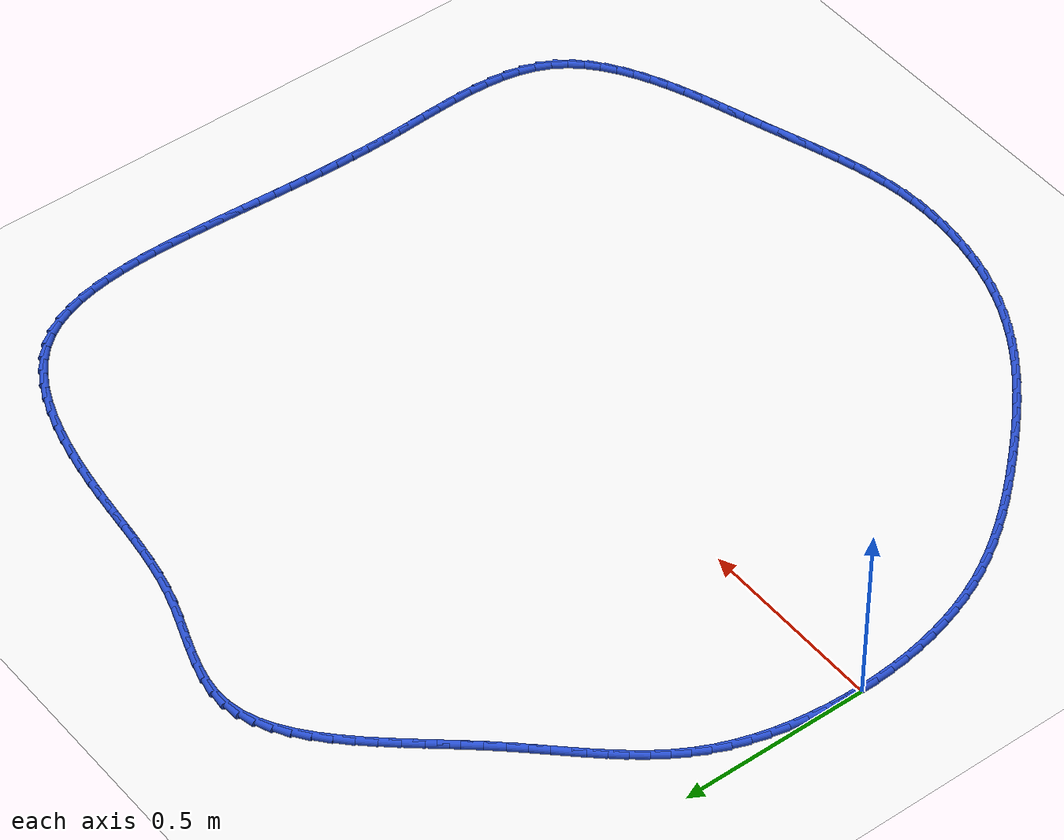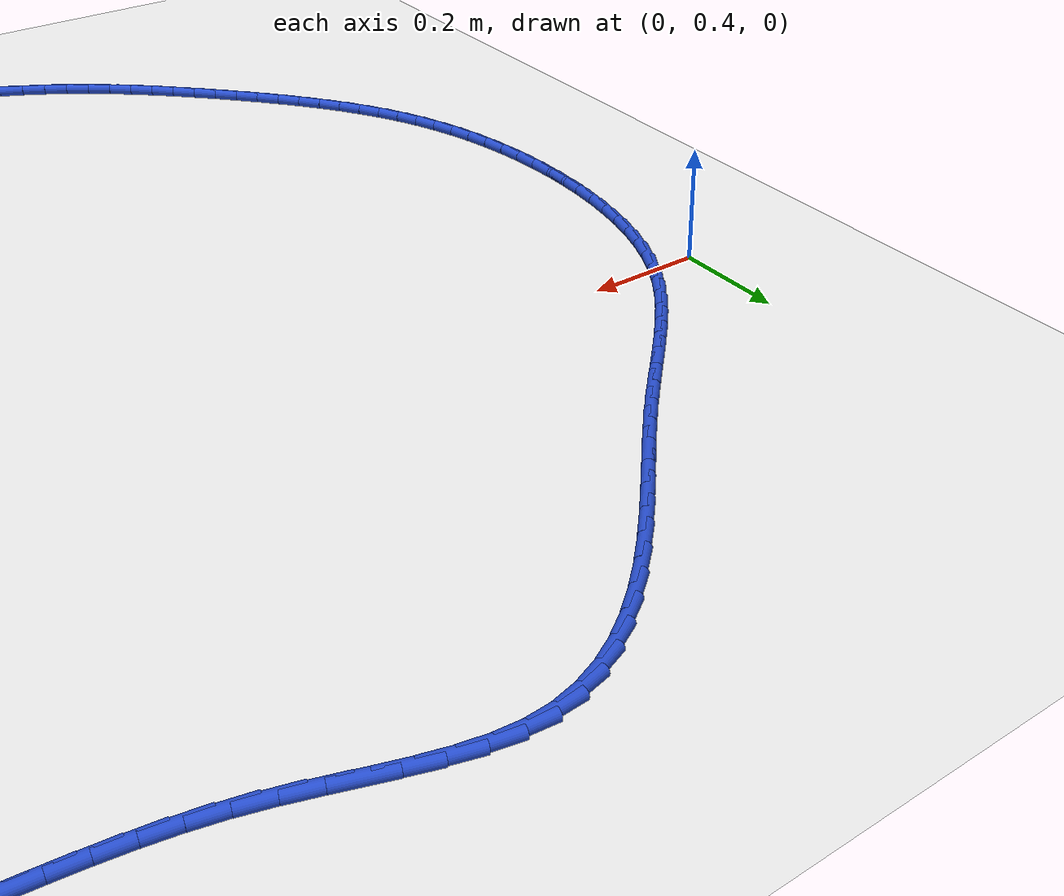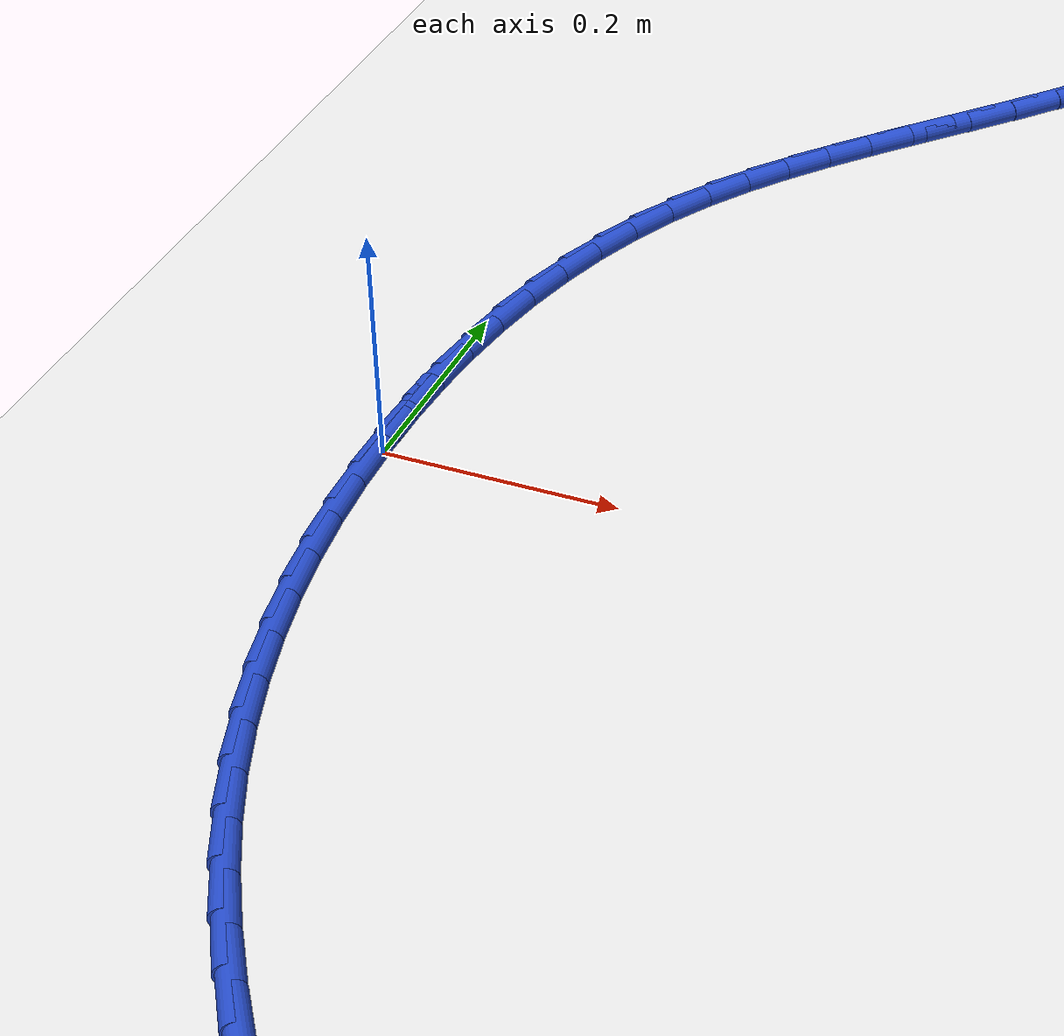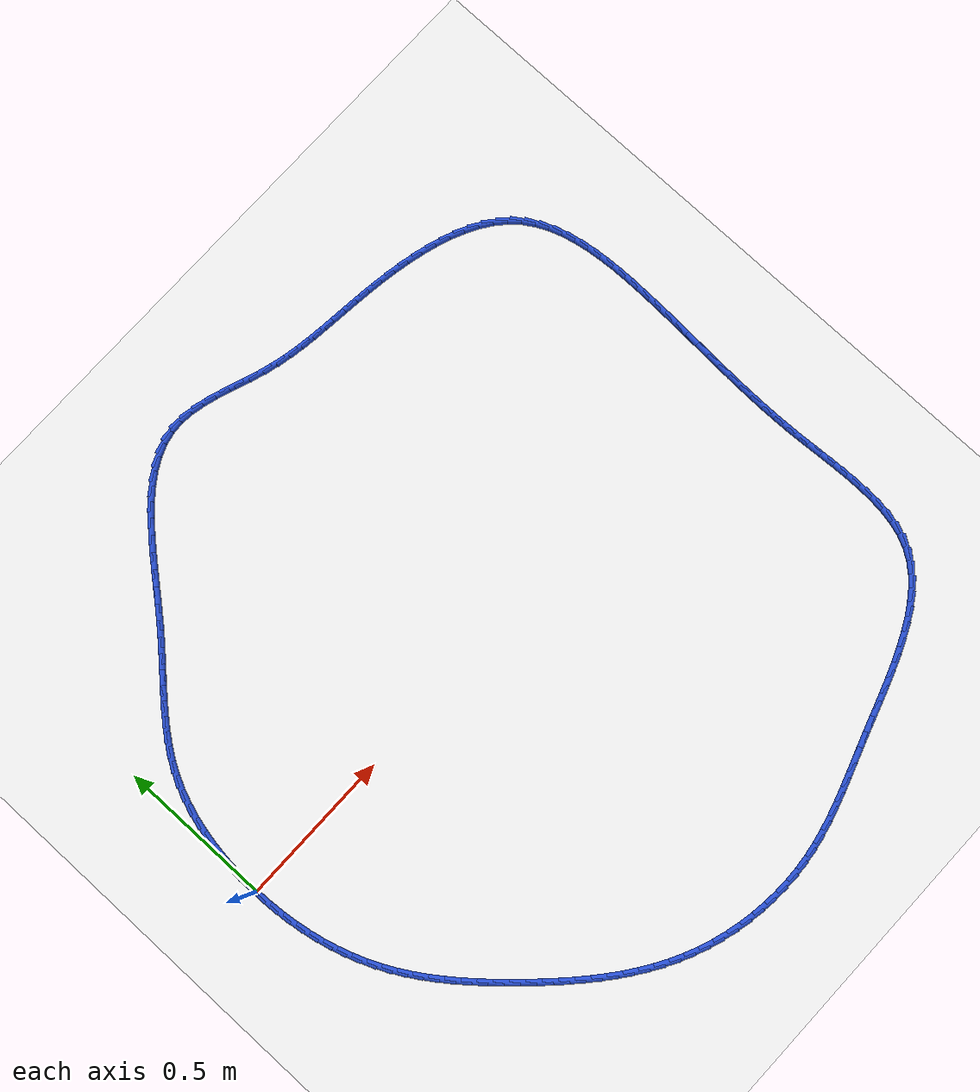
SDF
<sdf version="1.6">
 <world name="default">
  <light name="sun" type="directional">
   <pose>0 0 10 0 -0 0</pose>
   <diffuse>0.8 0.8 0.8 1</diffuse>
   <specular>0.2 0.2 0.2 1</specular>
   <attenuation>
    <range>1000</range>
    <constant>0.9</constant>
    <linear>0.01</linear>
    <quadratic>0.001</quadratic>
   </attenuation>
   <direction>-0.5 0.1 -0.9</direction>
  </light>
  <model name="ground_plane">
   <static>1</static>
   <link name="link">
    <collision name="collision">
     <geometry><plane><normal>0 0 1</normal><size>100 100</size></plane></geometry>
     <surface><friction><ode><mu>100</mu><mu2>50</mu2></ode></friction></surface>
    </collision>
    <visual name="visual">
     <cast_shadows>0</cast_shadows>
     <geometry><plane><normal>0 0 1</normal><size>100 100</size></plane></geometry>
     <material>
      <script><uri>file://media/materials/scripts/gazebo.material</uri><name>Gazebo/WhiteGlow</name></script>
     </material>
    </visual>
   </link>
  </model>
  <gravity>0 0 -9.8</gravity>
  <magnetic_field>6e-06 2.3e-05 -4.2e-05</magnetic_field>
  <atmosphere type="adiabatic"/>
  <physics name="default_physics" default="0" type="ode">
   <max_step_size>0.001</max_step_size>
   <real_time_factor>1</real_time_factor>
   <real_time_update_rate>1000</real_time_update_rate>
  </physics>
  <scene><ambient>0.4 0.4 0.4 1</ambient><background>0.7 0.7 0.7 1</background><shadows>1</shadows></scene>
  <spherical_coordinates>
   <surface_model>EARTH_WGS84</surface_model>
   <latitude_deg>0</latitude_deg>
   <longitude_deg>0</longitude_deg>
   <elevation>0</elevation>
   <heading_deg>0</heading_deg>
  </spherical_coordinates>
  <model name="line">
   <link name="link_0">
    <pose>-2.7755575615628914e-17 5.551115123125783e-17 0.01 0 1.57 1.5577472647489992</pose>
    <collision name="collision">
     <geometry><cylinder><radius>0.01</radius><length>0.08</length></cylinder></geometry>
    </collision>
    <visual name="visual">
     <material>
      <script><name>Gazebo/Blue</name><uri>file://media/materials/scripts/gazebo.material</uri></script>
     </material>
     <geometry><cylinder><radius>0.01</radius><length>0.08</length></cylinder></geometry>
    </visual>
   </link>
   <link name="link_1">
    <pose>0.0006270178614802262 0.048048071941946394 0.01 0 1.57 1.5150571508433226</pose>
    <collision name="collision">
     <geometry><cylinder><radius>0.01</radius><length>0.08</length></cylinder></geometry>
    </collision>
    <visual name="visual">
     <material>
      <script><name>Gazebo/Blue</name><uri>file://media/materials/scripts/gazebo.material</uri></script>
     </material>
     <geometry><cylinder><radius>0.01</radius><length>0.08</length></cylinder></geometry>
    </visual>
   </link>
   <link name="link_2">
    <pose>0.003306523279857362 0.09607048799242425 0.01 0 1.57 1.4699026750207158</pose>
    <collision name="collision">
     <geometry><cylinder><radius>0.01</radius><length>0.08</length></cylinder></geometry>
    </collision>
    <visual name="visual">
     <material>
      <script><name>Gazebo/Blue</name><uri>file://media/materials/scripts/gazebo.material</uri></script>
     </material>
     <geometry><cylinder><radius>0.01</radius><length>0.08</length></cylinder></geometry>
    </visual>
   </link>
   <link name="link_3">
    <pose>0.008139195591979335 0.1438065246907644 0.01 0 1.57 1.4217368841431537</pose>
    <collision name="collision">
     <geometry><cylinder><radius>0.01</radius><length>0.08</length></cylinder></geometry>
    </collision>
    <visual name="visual">
     <material>
      <script><name>Gazebo/Blue</name><uri>file://media/materials/scripts/gazebo.material</uri></script>
     </material>
     <geometry><cylinder><radius>0.01</radius><length>0.08</length></cylinder></geometry>
    </visual>
   </link>
   <link name="link_4">
    <pose>0.015225714134694096 0.19099545857629785 0.01 0 1.57 1.369986135056164</pose>
    <collision name="collision">
     <geometry><cylinder><radius>0.01</radius><length>0.08</length></cylinder></geometry>
    </collision>
    <visual name="visual">
     <material>
      <script><name>Gazebo/Blue</name><uri>file://media/materials/scripts/gazebo.material</uri></script>
     </material>
     <geometry><cylinder><radius>0.01</radius><length>0.08</length></cylinder></geometry>
    </visual>
   </link>
   <link name="link_5">
    <pose>0.024666758244849603 0.2373765661883554 0.01 0 1.57 1.3140528449187738</pose>
    <collision name="collision">
     <geometry><cylinder><radius>0.01</radius><length>0.08</length></cylinder></geometry>
    </collision>
    <visual name="visual">
     <material>
      <script><name>Gazebo/Blue</name><uri>file://media/materials/scripts/gazebo.material</uri></script>
     </material>
     <geometry><cylinder><radius>0.01</radius><length>0.08</length></cylinder></geometry>
    </visual>
   </link>
   <link name="link_6">
    <pose>0.03656300725929379 0.28268912406626784 0.01 0 1.57 1.253327688898295</pose>
    <collision name="collision">
     <geometry><cylinder><radius>0.01</radius><length>0.08</length></cylinder></geometry>
    </collision>
    <visual name="visual">
     <material>
      <script><name>Gazebo/Blue</name><uri>file://media/materials/scripts/gazebo.material</uri></script>
     </material>
     <geometry><cylinder><radius>0.01</radius><length>0.08</length></cylinder></geometry>
    </visual>
   </link>
   <link name="link_7">
    <pose>0.05101514051487464 0.32667240874936626 0.01 0 1.57 1.1872153947212785</pose>
    <collision name="collision">
     <geometry><cylinder><radius>0.01</radius><length>0.08</length></cylinder></geometry>
    </collision>
    <visual name="visual">
     <material>
      <script><name>Gazebo/Blue</name><uri>file://media/materials/scripts/gazebo.material</uri></script>
     </material>
     <geometry><cylinder><radius>0.01</radius><length>0.08</length></cylinder></geometry>
    </visual>
   </link>
   <link name="link_8">
    <pose>0.06812383734844009 0.3690656967769814 0.01 0 1.57 1.1151799937240305</pose>
    <collision name="collision">
     <geometry><cylinder><radius>0.01</radius><length>0.08</length></cylinder></geometry>
    </collision>
    <visual name="visual">
     <material>
      <script><name>Gazebo/Blue</name><uri>file://media/materials/scripts/gazebo.material</uri></script>
     </material>
     <geometry><cylinder><radius>0.01</radius><length>0.08</length></cylinder></geometry>
    </visual>
   </link>
   <link name="link_9">
    <pose>0.08798975042032907 0.4096083067578972 0.01 0 1.57 1.0400181833528062</pose>
    <collision name="collision">
     <geometry><cylinder><radius>0.01</radius><length>0.08</length></cylinder></geometry>
    </collision>
    <visual name="visual">
     <material>
      <script><name>Gazebo/Blue</name><uri>file://media/materials/scripts/gazebo.material</uri></script>
     </material>
     <geometry><cylinder><radius>0.01</radius><length>0.08</length></cylinder></geometry>
    </visual>
   </link>
   <link name="link_10">
    <pose>0.11062729218662108 0.44817556003720427 0.01 0 1.57 0.9726922970216155</pose>
    <collision name="collision">
     <geometry><cylinder><radius>0.01</radius><length>0.08</length></cylinder></geometry>
    </collision>
    <visual name="visual">
     <material>
      <script><name>Gazebo/Blue</name><uri>file://media/materials/scripts/gazebo.material</uri></script>
     </material>
     <geometry><cylinder><radius>0.01</radius><length>0.08</length></cylinder></geometry>
    </visual>
   </link>
   <link name="link_11">
    <pose>0.13577303329604676 0.48508094072159963 0.01 0 1.57 0.9165937269103684</pose>
    <collision name="collision">
     <geometry><cylinder><radius>0.01</radius><length>0.08</length></cylinder></geometry>
    </collision>
    <visual name="visual">
     <material>
      <script><name>Gazebo/Blue</name><uri>file://media/materials/scripts/gazebo.material</uri></script>
     </material>
     <geometry><cylinder><radius>0.01</radius><length>0.08</length></cylinder></geometry>
    </visual>
   </link>
   <link name="link_12">
    <pose>0.16310769901584693 0.5207260023368868 0.01 0 1.57 0.8724091532777977</pose>
    <collision name="collision">
     <geometry><cylinder><radius>0.01</radius><length>0.08</length></cylinder></geometry>
    </collision>
    <visual name="visual">
     <material>
      <script><name>Gazebo/Blue</name><uri>file://media/materials/scripts/gazebo.material</uri></script>
     </material>
     <geometry><cylinder><radius>0.01</radius><length>0.08</length></cylinder></geometry>
    </visual>
   </link>
   <link name="link_13">
    <pose>0.19231201461326236 0.5555122984088685 0.01 0 1.57 0.8402629300087076</pose>
    <collision name="collision">
     <geometry><cylinder><radius>0.01</radius><length>0.08</length></cylinder></geometry>
    </collision>
    <visual name="visual">
     <material>
      <script><name>Gazebo/Blue</name><uri>file://media/materials/scripts/gazebo.material</uri></script>
     </material>
     <geometry><cylinder><radius>0.01</radius><length>0.08</length></cylinder></geometry>
    </visual>
   </link>
   <link name="link_14">
    <pose>0.2230667053555341 0.5898413824633485 0.01 0 1.57 0.8199099824116222</pose>
    <collision name="collision">
     <geometry><cylinder><radius>0.01</radius><length>0.08</length></cylinder></geometry>
    </collision>
    <visual name="visual">
     <material>
      <script><name>Gazebo/Blue</name><uri>file://media/materials/scripts/gazebo.material</uri></script>
     </material>
     <geometry><cylinder><radius>0.01</radius><length>0.08</length></cylinder></geometry>
    </visual>
   </link>
   <link name="link_15">
    <pose>0.25505249650990275 0.6241148080261293 0.01 0 1.57 0.8108929619688039</pose>
    <collision name="collision">
     <geometry><cylinder><radius>0.01</radius><length>0.08</length></cylinder></geometry>
    </collision>
    <visual name="visual">
     <material>
      <script><name>Gazebo/Blue</name><uri>file://media/materials/scripts/gazebo.material</uri></script>
     </material>
     <geometry><cylinder><radius>0.01</radius><length>0.08</length></cylinder></geometry>
    </visual>
   </link>
   <link name="link_16">
    <pose>0.2879501133436093 0.6587341286230145 0.01 0 1.57 0.8126450472303505</pose>
    <collision name="collision">
     <geometry><cylinder><radius>0.01</radius><length>0.08</length></cylinder></geometry>
    </collision>
    <visual name="visual">
     <material>
      <script><name>Gazebo/Blue</name><uri>file://media/materials/scripts/gazebo.material</uri></script>
     </material>
     <geometry><cylinder><radius>0.01</radius><length>0.08</length></cylinder></geometry>
    </visual>
   </link>
   <link name="link_17">
    <pose>0.32144028112389456 0.694100897779807 0.01 0 1.57 0.8245409089728115</pose>
    <collision name="collision">
     <geometry><cylinder><radius>0.01</radius><length>0.08</length></cylinder></geometry>
    </collision>
    <visual name="visual">
     <material>
      <script><name>Gazebo/Blue</name><uri>file://media/materials/scripts/gazebo.material</uri></script>
     </material>
     <geometry><cylinder><radius>0.01</radius><length>0.08</length></cylinder></geometry>
    </visual>
   </link>
   <link name="link_18">
    <pose>0.35520372511799936 0.73061666902231 0.01 0 1.57 0.8452997351876824</pose>
    <collision name="collision">
     <geometry><cylinder><radius>0.01</radius><length>0.08</length></cylinder></geometry>
    </collision>
    <visual name="visual">
     <material>
      <script><name>Gazebo/Blue</name><uri>file://media/materials/scripts/gazebo.material</uri></script>
     </material>
     <geometry><cylinder><radius>0.01</radius><length>0.08</length></cylinder></geometry>
    </visual>
   </link>
   <link name="link_19">
    <pose>0.38893419495520126 0.7686511194605623 0.01 0 1.57 0.863937119515582</pose>
    <collision name="collision">
     <geometry><cylinder><radius>0.01</radius><length>0.08</length></cylinder></geometry>
    </collision>
    <visual name="visual">
     <material>
      <script><name>Gazebo/Blue</name><uri>file://media/materials/scripts/gazebo.material</uri></script>
     </material>
     <geometry><cylinder><radius>0.01</radius><length>0.08</length></cylinder></geometry>
    </visual>
   </link>
   <link name="link_20">
    <pose>0.4225539319222955 0.808014705334264 0.01 0 1.57 0.872078140182129</pose>
    <collision name="collision">
     <geometry><cylinder><radius>0.01</radius><length>0.08</length></cylinder></geometry>
    </collision>
    <visual name="visual">
     <material>
      <script><name>Gazebo/Blue</name><uri>file://media/materials/scripts/gazebo.material</uri></script>
     </material>
     <geometry><cylinder><radius>0.01</radius><length>0.08</length></cylinder></geometry>
    </visual>
   </link>
   <link name="link_21">
    <pose>0.4561800191463018 0.8480410181054147 0.01 0 1.57 0.869948432808069</pose>
    <collision name="collision">
     <geometry><cylinder><radius>0.01</radius><length>0.08</length></cylinder></geometry>
    </collision>
    <visual name="visual">
     <material>
      <script><name>Gazebo/Blue</name><uri>file://media/materials/scripts/gazebo.material</uri></script>
     </material>
     <geometry><cylinder><radius>0.01</radius><length>0.08</length></cylinder></geometry>
    </visual>
   </link>
   <link name="link_22">
    <pose>0.48993578056311893 0.8880483751966425 0.01 0 1.57 0.8575352679056768</pose>
    <collision name="collision">
     <geometry><cylinder><radius>0.01</radius><length>0.08</length></cylinder></geometry>
    </collision>
    <visual name="visual">
     <material>
      <script><name>Gazebo/Blue</name><uri>file://media/materials/scripts/gazebo.material</uri></script>
     </material>
     <geometry><cylinder><radius>0.01</radius><length>0.08</length></cylinder></geometry>
    </visual>
   </link>
   <link name="link_23">
    <pose>0.5239445401086457 0.9273550940305763 0.01 0 1.57 0.8343059135419395</pose>
    <collision name="collision">
     <geometry><cylinder><radius>0.01</radius><length>0.08</length></cylinder></geometry>
    </collision>
    <visual name="visual">
     <material>
      <script><name>Gazebo/Blue</name><uri>file://media/materials/scripts/gazebo.material</uri></script>
     </material>
     <geometry><cylinder><radius>0.01</radius><length>0.08</length></cylinder></geometry>
    </visual>
   </link>
   <link name="link_24">
    <pose>0.5583296217187803 0.9652794920298436 0.01 0 1.57 0.799188585918373</pose>
    <collision name="collision">
     <geometry><cylinder><radius>0.01</radius><length>0.08</length></cylinder></geometry>
    </collision>
    <visual name="visual">
     <material>
      <script><name>Gazebo/Blue</name><uri>file://media/materials/scripts/gazebo.material</uri></script>
     </material>
     <geometry><cylinder><radius>0.01</radius><length>0.08</length></cylinder></geometry>
    </visual>
   </link>
   <link name="link_25">
    <pose>0.5932143493294222 1.0011398866170735 0.01 0 1.57 0.7505404573366011</pose>
    <collision name="collision">
     <geometry><cylinder><radius>0.01</radius><length>0.08</length></cylinder></geometry>
    </collision>
    <visual name="visual">
     <material>
      <script><name>Gazebo/Blue</name><uri>file://media/materials/scripts/gazebo.material</uri></script>
     </material>
     <geometry><cylinder><radius>0.01</radius><length>0.08</length></cylinder></geometry>
    </visual>
   </link>
   <link name="link_26">
    <pose>0.6287220468764698 1.034254595214894 0.01 0 1.57 0.6861421622858155</pose>
    <collision name="collision">
     <geometry><cylinder><radius>0.01</radius><length>0.08</length></cylinder></geometry>
    </collision>
    <visual name="visual">
     <material>
      <script><name>Gazebo/Blue</name><uri>file://media/materials/scripts/gazebo.material</uri></script>
     </material>
     <geometry><cylinder><radius>0.01</radius><length>0.08</length></cylinder></geometry>
    </visual>
   </link>
   <link name="link_27">
    <pose>0.6649760382958217 1.0639419352459332 0.01 0 1.57 0.6033074314430158</pose>
    <collision name="collision">
     <geometry><cylinder><radius>0.01</radius><length>0.08</length></cylinder></geometry>
    </collision>
    <visual name="visual">
     <material>
      <script><name>Gazebo/Blue</name><uri>file://media/materials/scripts/gazebo.material</uri></script>
     </material>
     <geometry><cylinder><radius>0.01</radius><length>0.08</length></cylinder></geometry>
    </visual>
   </link>
   <link name="link_28">
    <pose>0.7020996475233767 1.0895202241328197 0.01 0 1.57 0.4992801802848108</pose>
    <collision name="collision">
     <geometry><cylinder><radius>0.01</radius><length>0.08</length></cylinder></geometry>
    </collision>
    <visual name="visual">
     <material>
      <script><name>Gazebo/Blue</name><uri>file://media/materials/scripts/gazebo.material</uri></script>
     </material>
     <geometry><cylinder><radius>0.01</radius><length>0.08</length></cylinder></geometry>
    </visual>
   </link>
   <link name="link_29">
    <pose>0.7402161984950337 1.1103077792981817 0.01 0 1.57 0.37217329856221465</pose>
    <collision name="collision">
     <geometry><cylinder><radius>0.01</radius><length>0.08</length></cylinder></geometry>
    </collision>
    <visual name="visual">
     <material>
      <script><name>Gazebo/Blue</name><uri>file://media/materials/scripts/gazebo.material</uri></script>
     </material>
     <geometry><cylinder><radius>0.01</radius><length>0.08</length></cylinder></geometry>
    </visual>
   </link>
   <link name="link_30">
    <pose>0.7794490151466912 1.1256229181646475 0.01 0 1.57 0.22260162466793534</pose>
    <collision name="collision">
     <geometry><cylinder><radius>0.01</radius><length>0.08</length></cylinder></geometry>
    </collision>
    <visual name="visual">
     <material>
      <script><name>Gazebo/Blue</name><uri>file://media/materials/scripts/gazebo.material</uri></script>
     </material>
     <geometry><cylinder><radius>0.01</radius><length>0.08</length></cylinder></geometry>
    </visual>
   </link>
   <link name="link_31">
    <pose>0.8199214214142483 1.1347839581548453 0.01 0 1.57 0.05574962236098516</pose>
    <collision name="collision">
     <geometry><cylinder><radius>0.01</radius><length>0.08</length></cylinder></geometry>
    </collision>
    <visual name="visual">
     <material>
      <script><name>Gazebo/Blue</name><uri>file://media/materials/scripts/gazebo.material</uri></script>
     </material>
     <geometry><cylinder><radius>0.01</radius><length>0.08</length></cylinder></geometry>
    </visual>
   </link>
   <link name="link_32">
    <pose>0.8617550495700701 1.1371185863184745 0.01 0 1.57 -0.1016440189844402</pose>
    <collision name="collision">
     <geometry><cylinder><radius>0.01</radius><length>0.08</length></cylinder></geometry>
    </collision>
    <visual name="visual">
     <material>
      <script><name>Gazebo/Blue</name><uri>file://media/materials/scripts/gazebo.material</uri></script>
     </material>
     <geometry><cylinder><radius>0.01</radius><length>0.08</length></cylinder></geometry>
    </visual>
   </link>
   <link name="link_33">
    <pose>0.904934314795307 1.1327144948406727 0.01 0 1.57 -0.21669088361511035</pose>
    <collision name="collision">
     <geometry><cylinder><radius>0.01</radius><length>0.08</length></cylinder></geometry>
    </collision>
    <visual name="visual">
     <material>
      <script><name>Gazebo/Blue</name><uri>file://media/materials/scripts/gazebo.material</uri></script>
     </material>
     <geometry><cylinder><radius>0.01</radius><length>0.08</length></cylinder></geometry>
    </visual>
   </link>
   <link name="link_34">
    <pose>0.9492073823655433 1.1229678946915609 0.01 0 1.57 -0.29219035805426574</pose>
    <collision name="collision">
     <geometry><cylinder><radius>0.01</radius><length>0.08</length></cylinder></geometry>
    </collision>
    <visual name="visual">
     <material>
      <script><name>Gazebo/Blue</name><uri>file://media/materials/scripts/gazebo.material</uri></script>
     </material>
     <geometry><cylinder><radius>0.01</radius><length>0.08</length></cylinder></geometry>
    </visual>
   </link>
   <link name="link_35">
    <pose>0.9942990673730373 1.1094043266432783 0.01 0 1.57 -0.33438318686641527</pose>
    <collision name="collision">
     <geometry><cylinder><radius>0.01</radius><length>0.08</length></cylinder></geometry>
    </collision>
    <visual name="visual">
     <material>
      <script><name>Gazebo/Blue</name><uri>file://media/materials/scripts/gazebo.material</uri></script>
     </material>
     <geometry><cylinder><radius>0.01</radius><length>0.08</length></cylinder></geometry>
    </visual>
   </link>
   <link name="link_36">
    <pose>1.0399341849100483 1.0935493314679638 0.01 0 1.57 -0.34739939851795587</pose>
    <collision name="collision">
     <geometry><cylinder><radius>0.01</radius><length>0.08</length></cylinder></geometry>
    </collision>
    <visual name="visual">
     <material>
      <script><name>Gazebo/Blue</name><uri>file://media/materials/scripts/gazebo.material</uri></script>
     </material>
     <geometry><cylinder><radius>0.01</radius><length>0.08</length></cylinder></geometry>
    </visual>
   </link>
   <link name="link_37">
    <pose>1.0858375500688346 1.0769284499377583 0.01 0 1.57 -0.3327383756387815</pose>
    <collision name="collision">
     <geometry><cylinder><radius>0.01</radius><length>0.08</length></cylinder></geometry>
    </collision>
    <visual name="visual">
     <material>
      <script><name>Gazebo/Blue</name><uri>file://media/materials/scripts/gazebo.material</uri></script>
     </material>
     <geometry><cylinder><radius>0.01</radius><length>0.08</length></cylinder></geometry>
    </visual>
   </link>
   <link name="link_38">
    <pose>1.131733977941656 1.0610672228248004 0.01 0 1.57 -0.29002515084186375</pose>
    <collision name="collision">
     <geometry><cylinder><radius>0.01</radius><length>0.08</length></cylinder></geometry>
    </collision>
    <visual name="visual">
     <material>
      <script><name>Gazebo/Blue</name><uri>file://media/materials/scripts/gazebo.material</uri></script>
     </material>
     <geometry><cylinder><radius>0.01</radius><length>0.08</length></cylinder></geometry>
    </visual>
   </link>
   <link name="link_39">
    <pose>1.1773576845385618 1.047451275738747 0.01 0 1.57 -0.23508317169298842</pose>
    <collision name="collision">
     <geometry><cylinder><radius>0.01</radius><length>0.08</length></cylinder></geometry>
    </collision>
    <visual name="visual">
     <material>
      <script><name>Gazebo/Blue</name><uri>file://media/materials/scripts/gazebo.material</uri></script>
     </material>
     <geometry><cylinder><radius>0.01</radius><length>0.08</length></cylinder></geometry>
    </visual>
   </link>
   <link name="link_40">
    <pose>1.2226708702567777 1.0365982400933567 0.01 0 1.57 -0.18735950661556267</pose>
    <collision name="collision">
     <geometry><cylinder><radius>0.01</radius><length>0.08</length></cylinder></geometry>
    </collision>
    <visual name="visual">
     <material>
      <script><name>Gazebo/Blue</name><uri>file://media/materials/scripts/gazebo.material</uri></script>
     </material>
     <geometry><cylinder><radius>0.01</radius><length>0.08</length></cylinder></geometry>
    </visual>
   </link>
   <link name="link_41">
    <pose>1.2678704530945848 1.0280291646928867 0.01 0 1.57 -0.14922793312525176</pose>
    <collision name="collision">
     <geometry><cylinder><radius>0.01</radius><length>0.08</length></cylinder></geometry>
    </collision>
    <visual name="visual">
     <material>
      <script><name>Gazebo/Blue</name><uri>file://media/materials/scripts/gazebo.material</uri></script>
     </material>
     <geometry><cylinder><radius>0.01</radius><length>0.08</length></cylinder></geometry>
    </visual>
   </link>
   <link name="link_42">
    <pose>1.3131640989684659 1.0212194639779162 0.01 0 1.57 -0.12166534359309315</pose>
    <collision name="collision">
     <geometry><cylinder><radius>0.01</radius><length>0.08</length></cylinder></geometry>
    </collision>
    <visual name="visual">
     <material>
      <script><name>Gazebo/Blue</name><uri>file://media/materials/scripts/gazebo.material</uri></script>
     </material>
     <geometry><cylinder><radius>0.01</radius><length>0.08</length></cylinder></geometry>
    </visual>
   </link>
   <link name="link_43">
    <pose>1.358759473794905 1.0156445523890252 0.01 0 1.57 -0.1051252260184742</pose>
    <collision name="collision">
     <geometry><cylinder><radius>0.01</radius><length>0.08</length></cylinder></geometry>
    </collision>
    <visual name="visual">
     <material>
      <script><name>Gazebo/Blue</name><uri>file://media/materials/scripts/gazebo.material</uri></script>
     </material>
     <geometry><cylinder><radius>0.01</radius><length>0.08</length></cylinder></geometry>
    </visual>
   </link>
   <link name="link_44">
    <pose>1.404864243490385 1.0107798443667928 0.01 0 1.57 -0.09960324648268445</pose>
    <collision name="collision">
     <geometry><cylinder><radius>0.01</radius><length>0.08</length></cylinder></geometry>
    </collision>
    <visual name="visual">
     <material>
      <script><name>Gazebo/Blue</name><uri>file://media/materials/scripts/gazebo.material</uri></script>
     </material>
     <geometry><cylinder><radius>0.01</radius><length>0.08</length></cylinder></geometry>
    </visual>
   </link>
   <link name="link_45">
    <pose>1.4516860739713886 1.0061007543517984 0.01 0 1.57 -0.10471337876252852</pose>
    <collision name="collision">
     <geometry><cylinder><radius>0.01</radius><length>0.08</length></cylinder></geometry>
    </collision>
    <visual name="visual">
     <material>
      <script><name>Gazebo/Blue</name><uri>file://media/materials/scripts/gazebo.material</uri></script>
     </material>
     <geometry><cylinder><radius>0.01</radius><length>0.08</length></cylinder></geometry>
    </visual>
   </link>
   <link name="link_46">
    <pose>1.4994326311543997 1.001082696784622 0.01 0 1.57 -0.11947354042110299</pose>
    <collision name="collision">
     <geometry><cylinder><radius>0.01</radius><length>0.08</length></cylinder></geometry>
    </collision>
    <visual name="visual">
     <material>
      <script><name>Gazebo/Blue</name><uri>file://media/materials/scripts/gazebo.material</uri></script>
     </material>
     <geometry><cylinder><radius>0.01</radius><length>0.08</length></cylinder></geometry>
    </visual>
   </link>
   <link name="link_47">
    <pose>1.5482549897434164 0.9952218041959419 0.01 0 1.57 -0.14101472048046151</pose>
    <collision name="collision">
     <geometry><cylinder><radius>0.01</radius><length>0.08</length></cylinder></geometry>
    </collision>
    <visual name="visual">
     <material>
      <script><name>Gazebo/Blue</name><uri>file://media/materials/scripts/gazebo.material</uri></script>
     </material>
     <geometry><cylinder><radius>0.01</radius><length>0.08</length></cylinder></geometry>
    </visual>
   </link>
   <link name="link_48">
    <pose>1.5978457684811063 0.9881820502263224 0.01 0 1.57 -0.16843367093007244</pose>
    <collision name="collision">
     <geometry><cylinder><radius>0.01</radius><length>0.08</length></cylinder></geometry>
    </collision>
    <visual name="visual">
     <material>
      <script><name>Gazebo/Blue</name><uri>file://media/materials/scripts/gazebo.material</uri></script>
     </material>
     <geometry><cylinder><radius>0.01</radius><length>0.08</length></cylinder></geometry>
    </visual>
   </link>
   <link name="link_49">
    <pose>1.6476752425139827 0.9797088086923605 0.01 0 1.57 -0.20230975728410908</pose>
    <collision name="collision">
     <geometry><cylinder><radius>0.01</radius><length>0.08</length></cylinder></geometry>
    </collision>
    <visual name="visual">
     <material>
      <script><name>Gazebo/Blue</name><uri>file://media/materials/scripts/gazebo.material</uri></script>
     </material>
     <geometry><cylinder><radius>0.01</radius><length>0.08</length></cylinder></geometry>
    </visual>
   </link>
   <link name="link_50">
    <pose>1.6972122216306658 0.9695479898793989 0.01 0 1.57 -0.24351288759406114</pose>
    <collision name="collision">
     <geometry><cylinder><radius>0.01</radius><length>0.08</length></cylinder></geometry>
    </collision>
    <visual name="visual">
     <material>
      <script><name>Gazebo/Blue</name><uri>file://media/materials/scripts/gazebo.material</uri></script>
     </material>
     <geometry><cylinder><radius>0.01</radius><length>0.08</length></cylinder></geometry>
    </visual>
   </link>
   <link name="link_51">
    <pose>1.7459255156197768 0.9574455040727804 0.01 0 1.57 -0.29321324230423373</pose>
    <collision name="collision">
     <geometry><cylinder><radius>0.01</radius><length>0.08</length></cylinder></geometry>
    </collision>
    <visual name="visual">
     <material>
      <script><name>Gazebo/Blue</name><uri>file://media/materials/scripts/gazebo.material</uri></script>
     </material>
     <geometry><cylinder><radius>0.01</radius><length>0.08</length></cylinder></geometry>
    </visual>
   </link>
   <link name="link_52">
    <pose>1.7932839342699367 0.9431472615578478 0.01 0 1.57 -0.35289582932010755</pose>
    <collision name="collision">
     <geometry><cylinder><radius>0.01</radius><length>0.08</length></cylinder></geometry>
    </collision>
    <visual name="visual">
     <material>
      <script><name>Gazebo/Blue</name><uri>file://media/materials/scripts/gazebo.material</uri></script>
     </material>
     <geometry><cylinder><radius>0.01</radius><length>0.08</length></cylinder></geometry>
    </visual>
   </link>
   <link name="link_53">
    <pose>1.8387562873697667 0.926399172619944 0.01 0 1.57 -0.42434463139012923</pose>
    <collision name="collision">
     <geometry><cylinder><radius>0.01</radius><length>0.08</length></cylinder></geometry>
    </collision>
    <visual name="visual">
     <material>
      <script><name>Gazebo/Blue</name><uri>file://media/materials/scripts/gazebo.material</uri></script>
     </material>
     <geometry><cylinder><radius>0.01</radius><length>0.08</length></cylinder></geometry>
    </visual>
   </link>
   <link name="link_54">
    <pose>1.881811384707888 0.9069471475444115 0.01 0 1.57 -0.50954496203695</pose>
    <collision name="collision">
     <geometry><cylinder><radius>0.01</radius><length>0.08</length></cylinder></geometry>
    </collision>
    <visual name="visual">
     <material>
      <script><name>Gazebo/Blue</name><uri>file://media/materials/scripts/gazebo.material</uri></script>
     </material>
     <geometry><cylinder><radius>0.01</radius><length>0.08</length></cylinder></geometry>
    </visual>
   </link>
   <link name="link_55">
    <pose>1.9219180360729196 0.8845370966165932 0.01 0 1.57 -0.6104190847306017</pose>
    <collision name="collision">
     <geometry><cylinder><radius>0.01</radius><length>0.08</length></cylinder></geometry>
    </collision>
    <visual name="visual">
     <material>
      <script><name>Gazebo/Blue</name><uri>file://media/materials/scripts/gazebo.material</uri></script>
     </material>
     <geometry><cylinder><radius>0.01</radius><length>0.08</length></cylinder></geometry>
    </visual>
   </link>
   <link name="link_56">
    <pose>1.9585450512534845 0.8589149301218324 0.01 0 1.57 -0.7282876243490881</pose>
    <collision name="collision">
     <geometry><cylinder><radius>0.01</radius><length>0.08</length></cylinder></geometry>
    </collision>
    <visual name="visual">
     <material>
      <script><name>Gazebo/Blue</name><uri>file://media/materials/scripts/gazebo.material</uri></script>
     </material>
     <geometry><cylinder><radius>0.01</radius><length>0.08</length></cylinder></geometry>
    </visual>
   </link>
   <link name="link_57">
    <pose>1.9911612400382028 0.8298265583454714 0.01 0 1.57 -0.8630048379674841</pose>
    <collision name="collision">
     <geometry><cylinder><radius>0.01</radius><length>0.08</length></cylinder></geometry>
    </collision>
    <visual name="visual">
     <material>
      <script><name>Gazebo/Blue</name><uri>file://media/materials/scripts/gazebo.material</uri></script>
     </material>
     <geometry><cylinder><radius>0.01</radius><length>0.08</length></cylinder></geometry>
    </visual>
   </link>
   <link name="link_58">
    <pose>2.0192354521282048 0.7970179222257225 0.01 0 1.57 -1.0062319117616587</pose>
    <collision name="collision">
     <geometry><cylinder><radius>0.01</radius><length>0.08</length></cylinder></geometry>
    </collision>
    <visual name="visual">
     <material>
      <script><name>Gazebo/Blue</name><uri>file://media/materials/scripts/gazebo.material</uri></script>
     </material>
     <geometry><cylinder><radius>0.01</radius><length>0.08</length></cylinder></geometry>
    </visual>
   </link>
   <link name="link_59">
    <pose>2.0424346895046384 0.7603871439656591 0.01 0 1.57 -1.1349974393412567</pose>
    <collision name="collision">
     <geometry><cylinder><radius>0.01</radius><length>0.08</length></cylinder></geometry>
    </collision>
    <visual name="visual">
     <material>
      <script><name>Gazebo/Blue</name><uri>file://media/materials/scripts/gazebo.material</uri></script>
     </material>
     <geometry><cylinder><radius>0.01</radius><length>0.08</length></cylinder></geometry>
    </visual>
   </link>
   <link name="link_60">
    <pose>2.0610840276686417 0.7203377472738673 0.01 0 1.57 -1.2440044031408821</pose>
    <collision name="collision">
     <geometry><cylinder><radius>0.01</radius><length>0.08</length></cylinder></geometry>
    </collision>
    <visual name="visual">
     <material>
      <script><name>Gazebo/Blue</name><uri>file://media/materials/scripts/gazebo.material</uri></script>
     </material>
     <geometry><cylinder><radius>0.01</radius><length>0.08</length></cylinder></geometry>
    </visual>
   </link>
   <link name="link_61">
    <pose>2.075644977460609 0.6773780384155502 0.01 0 1.57 -1.3342664586276411</pose>
    <collision name="collision">
     <geometry><cylinder><radius>0.01</radius><length>0.08</length></cylinder></geometry>
    </collision>
    <visual name="visual">
     <material>
      <script><name>Gazebo/Blue</name><uri>file://media/materials/scripts/gazebo.material</uri></script>
     </material>
     <geometry><cylinder><radius>0.01</radius><length>0.08</length></cylinder></geometry>
    </visual>
   </link>
   <link name="link_62">
    <pose>2.0865790497209384 0.632016323655912 0.01 0 1.57 -1.407855604424198</pose>
    <collision name="collision">
     <geometry><cylinder><radius>0.01</radius><length>0.08</length></cylinder></geometry>
    </collision>
    <visual name="visual">
     <material>
      <script><name>Gazebo/Blue</name><uri>file://media/materials/scripts/gazebo.material</uri></script>
     </material>
     <geometry><cylinder><radius>0.01</radius><length>0.08</length></cylinder></geometry>
    </visual>
   </link>
   <link name="link_63">
    <pose>2.0943477552900247 0.5847609092601567 0.01 0 1.57 -1.4670426512309898</pose>
    <collision name="collision">
     <geometry><cylinder><radius>0.01</radius><length>0.08</length></cylinder></geometry>
    </collision>
    <visual name="visual">
     <material>
      <script><name>Gazebo/Blue</name><uri>file://media/materials/scripts/gazebo.material</uri></script>
     </material>
     <geometry><cylinder><radius>0.01</radius><length>0.08</length></cylinder></geometry>
    </visual>
   </link>
   <link name="link_64">
    <pose>2.099412605008264 0.5361201014934877 0.01 0 1.57 -1.5138582457123684</pose>
    <collision name="collision">
     <geometry><cylinder><radius>0.01</radius><length>0.08</length></cylinder></geometry>
    </collision>
    <visual name="visual">
     <material>
      <script><name>Gazebo/Blue</name><uri>file://media/materials/scripts/gazebo.material</uri></script>
     </material>
     <geometry><cylinder><radius>0.01</radius><length>0.08</length></cylinder></geometry>
    </visual>
   </link>
   <link name="link_65">
    <pose>2.102235109716053 0.48660220662110876 0.01 0 1.57 -1.5499186240576708</pose>
    <collision name="collision">
     <geometry><cylinder><radius>0.01</radius><length>0.08</length></cylinder></geometry>
    </collision>
    <visual name="visual">
     <material>
      <script><name>Gazebo/Blue</name><uri>file://media/materials/scripts/gazebo.material</uri></script>
     </material>
     <geometry><cylinder><radius>0.01</radius><length>0.08</length></cylinder></geometry>
    </visual>
   </link>
   <link name="link_66">
    <pose>2.103276780253787 0.4367155309082238 0.01 0 1.57 1.5652151044063933</pose>
    <collision name="collision">
     <geometry><cylinder><radius>0.01</radius><length>0.08</length></cylinder></geometry>
    </collision>
    <visual name="visual">
     <material>
      <script><name>Gazebo/Blue</name><uri>file://media/materials/scripts/gazebo.material</uri></script>
     </material>
     <geometry><cylinder><radius>0.01</radius><length>0.08</length></cylinder></geometry>
    </visual>
   </link>
   <link name="link_67">
    <pose>2.102999127461863 0.38696838062003613 0.01 0 1.57 1.5476605720555994</pose>
    <collision name="collision">
     <geometry><cylinder><radius>0.01</radius><length>0.08</length></cylinder></geometry>
    </collision>
    <visual name="visual">
     <material>
      <script><name>Gazebo/Blue</name><uri>file://media/materials/scripts/gazebo.material</uri></script>
     </material>
     <geometry><cylinder><radius>0.01</radius><length>0.08</length></cylinder></geometry>
    </visual>
   </link>
   <link name="link_68">
    <pose>2.101862942859436 0.3378676752942488 0.01 0 1.57 1.536777372102222</pose>
    <collision name="collision">
     <geometry><cylinder><radius>0.01</radius><length>0.08</length></cylinder></geometry>
    </collision>
    <visual name="visual">
     <material>
      <script><name>Gazebo/Blue</name><uri>file://media/materials/scripts/gazebo.material</uri></script>
     </material>
     <geometry><cylinder><radius>0.01</radius><length>0.08</length></cylinder></geometry>
    </visual>
   </link>
   <link name="link_69">
    <pose>2.10022432631809 0.28971850699723806 0.01 0 1.57 1.528572875986556</pose>
    <collision name="collision">
     <geometry><cylinder><radius>0.01</radius><length>0.08</length></cylinder></geometry>
    </collision>
    <visual name="visual">
     <material>
      <script><name>Gazebo/Blue</name><uri>file://media/materials/scripts/gazebo.material</uri></script>
     </material>
     <geometry><cylinder><radius>0.01</radius><length>0.08</length></cylinder></geometry>
    </visual>
   </link>
   <link name="link_70">
    <pose>2.098225787533695 0.24241420271131434 0.01 0 1.57 1.522738871788107</pose>
    <collision name="collision">
     <geometry><cylinder><radius>0.01</radius><length>0.08</length></cylinder></geometry>
    </collision>
    <visual name="visual">
     <material>
      <script><name>Gazebo/Blue</name><uri>file://media/materials/scripts/gazebo.material</uri></script>
     </material>
     <geometry><cylinder><radius>0.01</radius><length>0.08</length></cylinder></geometry>
    </visual>
   </link>
   <link name="link_71">
    <pose>2.095983800264289 0.19579789661336694 0.01 0 1.57 1.519437537232453</pose>
    <collision name="collision">
     <geometry><cylinder><radius>0.01</radius><length>0.08</length></cylinder></geometry>
    </collision>
    <visual name="visual">
     <material>
      <script><name>Gazebo/Blue</name><uri>file://media/materials/scripts/gazebo.material</uri></script>
     </material>
     <geometry><cylinder><radius>0.01</radius><length>0.08</length></cylinder></geometry>
    </visual>
   </link>
   <link name="link_72">
    <pose>2.0936148382679147 0.14971272288028667 0.01 0 1.57 1.518788668155942</pose>
    <collision name="collision">
     <geometry><cylinder><radius>0.01</radius><length>0.08</length></cylinder></geometry>
    </collision>
    <visual name="visual">
     <material>
      <script><name>Gazebo/Blue</name><uri>file://media/materials/scripts/gazebo.material</uri></script>
     </material>
     <geometry><cylinder><radius>0.01</radius><length>0.08</length></cylinder></geometry>
    </visual>
   </link>
   <link name="link_73">
    <pose>2.091235375302609 0.10400181568896301 0.01 0 1.57 1.5208639170561606</pose>
    <collision name="collision">
     <geometry><cylinder><radius>0.01</radius><length>0.08</length></cylinder></geometry>
    </collision>
    <visual name="visual">
     <material>
      <script><name>Gazebo/Blue</name><uri>file://media/materials/scripts/gazebo.material</uri></script>
     </material>
     <geometry><cylinder><radius>0.01</radius><length>0.08</length></cylinder></geometry>
    </visual>
   </link>
   <link name="link_74">
    <pose>2.0889618851264147 0.058508309216285956 0.01 0 1.57 1.525682571162585</pose>
    <collision name="collision">
     <geometry><cylinder><radius>0.01</radius><length>0.08</length></cylinder></geometry>
    </collision>
    <visual name="visual">
     <material>
      <script><name>Gazebo/Blue</name><uri>file://media/materials/scripts/gazebo.material</uri></script>
     </material>
     <geometry><cylinder><radius>0.01</radius><length>0.08</length></cylinder></geometry>
    </visual>
   </link>
   <link name="link_75">
    <pose>2.086910841497369 0.013075337639145257 0.01 0 1.57 1.5332091716858143</pose>
    <collision name="collision">
     <geometry><cylinder><radius>0.01</radius><length>0.08</length></cylinder></geometry>
    </collision>
    <visual name="visual">
     <material>
      <script><name>Gazebo/Blue</name><uri>file://media/materials/scripts/gazebo.material</uri></script>
     </material>
     <geometry><cylinder><radius>0.01</radius><length>0.08</length></cylinder></geometry>
    </visual>
   </link>
   <link name="link_76">
    <pose>2.0851987181735137 -0.03245396486556951 0.01 0 1.57 1.543353225734103</pose>
    <collision name="collision">
     <geometry><cylinder><radius>0.01</radius><length>0.08</length></cylinder></geometry>
    </collision>
    <visual name="visual">
     <material>
      <script><name>Gazebo/Blue</name><uri>file://media/materials/scripts/gazebo.material</uri></script>
     </material>
     <geometry><cylinder><radius>0.01</radius><length>0.08</length></cylinder></geometry>
    </visual>
   </link>
   <link name="link_77">
    <pose>2.083941988912887 -0.07823646412096802 0.01 0 1.57 1.5559711853120826</pose>
    <collision name="collision">
     <geometry><cylinder><radius>0.01</radius><length>0.08</length></cylinder></geometry>
    </collision>
    <visual name="visual">
     <material>
      <script><name>Gazebo/Blue</name><uri>file://media/materials/scripts/gazebo.material</uri></script>
     </material>
     <geometry><cylinder><radius>0.01</radius><length>0.08</length></cylinder></geometry>
    </visual>
   </link>
   <link name="link_78">
    <pose>2.083257127473531 -0.12442902595015973 0.01 0 1.57 -1.5707219004072486</pose>
    <collision name="collision">
     <geometry><cylinder><radius>0.01</radius><length>0.08</length></cylinder></geometry>
    </collision>
    <visual name="visual">
     <material>
      <script><name>Gazebo/Blue</name><uri>file://media/materials/scripts/gazebo.material</uri></script>
     </material>
     <geometry><cylinder><radius>0.01</radius><length>0.08</length></cylinder></geometry>
    </visual>
   </link>
   <link name="link_79">
    <pose>2.083260607613483 -0.1711885161762562 0.01 0 1.57 -1.553775233454882</pose>
    <collision name="collision">
     <geometry><cylinder><radius>0.01</radius><length>0.08</length></cylinder></geometry>
    </collision>
    <visual name="visual">
     <material>
      <script><name>Gazebo/Blue</name><uri>file://media/materials/scripts/gazebo.material</uri></script>
     </material>
     <geometry><cylinder><radius>0.01</radius><length>0.08</length></cylinder></geometry>
    </visual>
   </link>
   <link name="link_80">
    <pose>2.0840689030907855 -0.21867180062236596 0.01 0 1.57 -1.5350500490795695</pose>
    <collision name="collision">
     <geometry><cylinder><radius>0.01</radius><length>0.08</length></cylinder></geometry>
    </collision>
    <visual name="visual">
     <material>
      <script><name>Gazebo/Blue</name><uri>file://media/materials/scripts/gazebo.material</uri></script>
     </material>
     <geometry><cylinder><radius>0.01</radius><length>0.08</length></cylinder></geometry>
    </visual>
   </link>
   <link name="link_81">
    <pose>2.085798470335357 -0.26703573147210274 0.01 0 1.57 -1.517720080324469</pose>
    <collision name="collision">
     <geometry><cylinder><radius>0.01</radius><length>0.08</length></cylinder></geometry>
    </collision>
    <visual name="visual">
     <material>
      <script><name>Gazebo/Blue</name><uri>file://media/materials/scripts/gazebo.material</uri></script>
     </material>
     <geometry><cylinder><radius>0.01</radius><length>0.08</length></cylinder></geometry>
    </visual>
   </link>
   <link name="link_82">
    <pose>2.0884167461445657 -0.31631986295380154 0.01 0 1.57 -1.5114145491426505</pose>
    <collision name="collision">
     <geometry><cylinder><radius>0.01</radius><length>0.08</length></cylinder></geometry>
    </collision>
    <visual name="visual">
     <material>
      <script><name>Gazebo/Blue</name><uri>file://media/materials/scripts/gazebo.material</uri></script>
     </material>
     <geometry><cylinder><radius>0.01</radius><length>0.08</length></cylinder></geometry>
    </visual>
   </link>
   <link name="link_83">
    <pose>2.0913799040684906 -0.3661613182034126 0.01 0 1.57 -1.5176996360397241</pose>
    <collision name="collision">
     <geometry><cylinder><radius>0.01</radius><length>0.08</length></cylinder></geometry>
    </collision>
    <visual name="visual">
     <material>
      <script><name>Gazebo/Blue</name><uri>file://media/materials/scripts/gazebo.material</uri></script>
     </material>
     <geometry><cylinder><radius>0.01</radius><length>0.08</length></cylinder></geometry>
    </visual>
   </link>
   <link name="link_84">
    <pose>2.094034561278242 -0.41611098514733563 0.01 0 1.57 -1.5366870906105743</pose>
    <collision name="collision">
     <geometry><cylinder><radius>0.01</radius><length>0.08</length></cylinder></geometry>
    </collision>
    <visual name="visual">
     <material>
      <script><name>Gazebo/Blue</name><uri>file://media/materials/scripts/gazebo.material</uri></script>
     </material>
     <geometry><cylinder><radius>0.01</radius><length>0.08</length></cylinder></geometry>
    </visual>
   </link>
   <link name="link_85">
    <pose>2.095727334944926 -0.46571975171196783 0.01 0 1.57 -1.569208674036933</pose>
    <collision name="collision">
     <geometry><cylinder><radius>0.01</radius><length>0.08</length></cylinder></geometry>
    </collision>
    <visual name="visual">
     <material>
      <script><name>Gazebo/Blue</name><uri>file://media/materials/scripts/gazebo.material</uri></script>
     </material>
     <geometry><cylinder><radius>0.01</radius><length>0.08</length></cylinder></geometry>
    </visual>
   </link>
   <link name="link_86">
    <pose>2.0958048422396547 -0.5145385058237091 0.01 0 1.57 1.5247767401578185</pose>
    <collision name="collision">
     <geometry><cylinder><radius>0.01</radius><length>0.08</length></cylinder></geometry>
    </collision>
    <visual name="visual">
     <material>
      <script><name>Gazebo/Blue</name><uri>file://media/materials/scripts/gazebo.material</uri></script>
     </material>
     <geometry><cylinder><radius>0.01</radius><length>0.08</length></cylinder></geometry>
    </visual>
   </link>
   <link name="link_87">
    <pose>2.093613700333535 -0.5621181354089567 0.01 0 1.57 1.4598349640938602</pose>
    <collision name="collision">
     <geometry><cylinder><radius>0.01</radius><length>0.08</length></cylinder></geometry>
    </collision>
    <visual name="visual">
     <material>
      <script><name>Gazebo/Blue</name><uri>file://media/materials/scripts/gazebo.material</uri></script>
     </material>
     <geometry><cylinder><radius>0.01</radius><length>0.08</length></cylinder></geometry>
    </visual>
   </link>
   <link name="link_88">
    <pose>2.0885005263976786 -0.6080095283941087 0.01 0 1.57 1.374768487740471</pose>
    <collision name="collision">
     <geometry><cylinder><radius>0.01</radius><length>0.08</length></cylinder></geometry>
    </collision>
    <visual name="visual">
     <material>
      <script><name>Gazebo/Blue</name><uri>file://media/materials/scripts/gazebo.material</uri></script>
     </material>
     <geometry><cylinder><radius>0.01</radius><length>0.08</length></cylinder></geometry>
    </visual>
   </link>
   <link name="link_89">
    <pose>2.0798119376031905 -0.6517635727055644 0.01 0 1.57 1.2667496965277025</pose>
    <collision name="collision">
     <geometry><cylinder><radius>0.01</radius><length>0.08</length></cylinder></geometry>
    </collision>
    <visual name="visual">
     <material>
      <script><name>Gazebo/Blue</name><uri>file://media/materials/scripts/gazebo.material</uri></script>
     </material>
     <geometry><cylinder><radius>0.01</radius><length>0.08</length></cylinder></geometry>
    </visual>
   </link>
   <link name="link_90">
    <pose>2.066894551121184 -0.6929311562697221 0.01 0 1.57 1.1340695664018547</pose>
    <collision name="collision">
     <geometry><cylinder><radius>0.01</radius><length>0.08</length></cylinder></geometry>
    </collision>
    <visual name="visual">
     <material>
      <script><name>Gazebo/Blue</name><uri>file://media/materials/scripts/gazebo.material</uri></script>
     </material>
     <geometry><cylinder><radius>0.01</radius><length>0.08</length></cylinder></geometry>
    </visual>
   </link>
   <link name="link_91">
    <pose>2.0490949867210158 -0.7310631686291307 0.01 0 1.57 0.9840753918291316</pose>
    <collision name="collision">
     <geometry><cylinder><radius>0.01</radius><length>0.08</length></cylinder></geometry>
    </collision>
    <visual name="visual">
     <material>
      <script><name>Gazebo/Blue</name><uri>file://media/materials/scripts/gazebo.material</uri></script>
     </material>
     <geometry><cylinder><radius>0.01</radius><length>0.08</length></cylinder></geometry>
    </visual>
   </link>
   <link name="link_92">
    <pose>2.0259727996602925 -0.7658429484804289 0.01 0 1.57 0.8441773202392268</pose>
    <collision name="collision">
     <geometry><cylinder><radius>0.01</radius><length>0.08</length></cylinder></geometry>
    </collision>
    <visual name="visual">
     <material>
      <script><name>Gazebo/Blue</name><uri>file://media/materials/scripts/gazebo.material</uri></script>
     </material>
     <geometry><cylinder><radius>0.01</radius><length>0.08</length></cylinder></geometry>
    </visual>
   </link>
   <link name="link_93">
    <pose>1.9978811903860239 -0.79744749405464 0.01 0 1.57 0.7234038554634935</pose>
    <collision name="collision">
     <geometry><cylinder><radius>0.01</radius><length>0.08</length></cylinder></geometry>
    </collision>
    <visual name="visual">
     <material>
      <script><name>Gazebo/Blue</name><uri>file://media/materials/scripts/gazebo.material</uri></script>
     </material>
     <geometry><cylinder><radius>0.01</radius><length>0.08</length></cylinder></geometry>
    </visual>
   </link>
   <link name="link_94">
    <pose>1.9653582245256056 -0.8261687925729468 0.01 0 1.57 0.6223995451969639</pose>
    <collision name="collision">
     <geometry><cylinder><radius>0.01</radius><length>0.08</length></cylinder></geometry>
    </collision>
    <visual name="visual">
     <material>
      <script><name>Gazebo/Blue</name><uri>file://media/materials/scripts/gazebo.material</uri></script>
     </material>
     <geometry><cylinder><radius>0.01</radius><length>0.08</length></cylinder></geometry>
    </visual>
   </link>
   <link name="link_95">
    <pose>1.9289419677064323 -0.8522988312565305 0.01 0 1.57 0.5398253953865746</pose>
    <collision name="collision">
     <geometry><cylinder><radius>0.01</radius><length>0.08</length></cylinder></geometry>
    </collision>
    <visual name="visual">
     <material>
      <script><name>Gazebo/Blue</name><uri>file://media/materials/scripts/gazebo.material</uri></script>
     </material>
     <geometry><cylinder><radius>0.01</radius><length>0.08</length></cylinder></geometry>
    </visual>
   </link>
   <link name="link_96">
    <pose>1.8891704855559008 -0.8761295973265729 0.01 0 1.57 0.4735380522900093</pose>
    <collision name="collision">
     <geometry><cylinder><radius>0.01</radius><length>0.08</length></cylinder></geometry>
    </collision>
    <visual name="visual">
     <material>
      <script><name>Gazebo/Blue</name><uri>file://media/materials/scripts/gazebo.material</uri></script>
     </material>
     <geometry><cylinder><radius>0.01</radius><length>0.08</length></cylinder></geometry>
    </visual>
   </link>
   <link name="link_97">
    <pose>1.8465818437014039 -0.8979530780042566 0.01 0 1.57 0.42132751541206054</pose>
    <collision name="collision">
     <geometry><cylinder><radius>0.01</radius><length>0.08</length></cylinder></geometry>
    </collision>
    <visual name="visual">
     <material>
      <script><name>Gazebo/Blue</name><uri>file://media/materials/scripts/gazebo.material</uri></script>
     </material>
     <geometry><cylinder><radius>0.01</radius><length>0.08</length></cylinder></geometry>
    </visual>
   </link>
   <link name="link_98">
    <pose>1.8017141077703387 -0.9180612605107625 0.01 0 1.57 0.38127123882235514</pose>
    <collision name="collision">
     <geometry><cylinder><radius>0.01</radius><length>0.08</length></cylinder></geometry>
    </collision>
    <visual name="visual">
     <material>
      <script><name>Gazebo/Blue</name><uri>file://media/materials/scripts/gazebo.material</uri></script>
     </material>
     <geometry><cylinder><radius>0.01</radius><length>0.08</length></cylinder></geometry>
    </visual>
   </link>
   <link name="link_99">
    <pose>1.7551053433900987 -0.9367461320672733 0.01 0 1.57 0.3518610521875989</pose>
    <collision name="collision">
     <geometry><cylinder><radius>0.01</radius><length>0.08</length></cylinder></geometry>
    </collision>
    <visual name="visual">
     <material>
      <script><name>Gazebo/Blue</name><uri>file://media/materials/scripts/gazebo.material</uri></script>
     </material>
     <geometry><cylinder><radius>0.01</radius><length>0.08</length></cylinder></geometry>
    </visual>
   </link>
   <link name="link_100">
    <pose>1.7072936161880805 -0.954299679894971 0.01 0 1.57 0.332025063910949</pose>
    <collision name="collision">
     <geometry><cylinder><radius>0.01</radius><length>0.08</length></cylinder></geometry>
    </collision>
    <visual name="visual">
     <material>
      <script><name>Gazebo/Blue</name><uri>file://media/materials/scripts/gazebo.material</uri></script>
     </material>
     <geometry><cylinder><radius>0.01</radius><length>0.08</length></cylinder></geometry>
    </visual>
   </link>
   <link name="link_101">
    <pose>1.658816991791679 -0.9710138912150363 0.01 0 1.57 0.32111546606502694</pose>
    <collision name="collision">
     <geometry><cylinder><radius>0.01</radius><length>0.08</length></cylinder></geometry>
    </collision>
    <visual name="visual">
     <material>
      <script><name>Gazebo/Blue</name><uri>file://media/materials/scripts/gazebo.material</uri></script>
     </material>
     <geometry><cylinder><radius>0.01</radius><length>0.08</length></cylinder></geometry>
    </visual>
   </link>
   <link name="link_102">
    <pose>1.6102135358282885 -0.9871807532486524 0.01 0 1.57 0.3188985013811591</pose>
    <collision name="collision">
     <geometry><cylinder><radius>0.01</radius><length>0.08</length></cylinder></geometry>
    </collision>
    <visual name="visual">
     <material>
      <script><name>Gazebo/Blue</name><uri>file://media/materials/scripts/gazebo.material</uri></script>
     </material>
     <geometry><cylinder><radius>0.01</radius><length>0.08</length></cylinder></geometry>
    </visual>
   </link>
   <link name="link_103">
    <pose>1.562021313925305 -1.0030922532170008 0.01 0 1.57 0.3251683154801974</pose>
    <collision name="collision">
     <geometry><cylinder><radius>0.01</radius><length>0.08</length></cylinder></geometry>
    </collision>
    <visual name="visual">
     <material>
      <script><name>Gazebo/Blue</name><uri>file://media/materials/scripts/gazebo.material</uri></script>
     </material>
     <geometry><cylinder><radius>0.01</radius><length>0.08</length></cylinder></geometry>
    </visual>
   </link>
   <link name="link_104">
    <pose>1.514760245777732 -1.0190256224884353 0.01 0 1.57 0.33204290027987793</pose>
    <collision name="collision">
     <geometry><cylinder><radius>0.01</radius><length>0.08</length></cylinder></geometry>
    </collision>
    <visual name="visual">
     <material>
      <script><name>Gazebo/Blue</name><uri>file://media/materials/scripts/gazebo.material</uri></script>
     </material>
     <geometry><cylinder><radius>0.01</radius><length>0.08</length></cylinder></geometry>
    </visual>
   </link>
   <link name="link_105">
    <pose>1.4685730709973723 -1.0349513783051474 0.01 0 1.57 0.33145169681392794</pose>
    <collision name="collision">
     <geometry><cylinder><radius>0.01</radius><length>0.08</length></cylinder></geometry>
    </collision>
    <visual name="visual">
     <material>
      <script><name>Gazebo/Blue</name><uri>file://media/materials/scripts/gazebo.material</uri></script>
     </material>
     <geometry><cylinder><radius>0.01</radius><length>0.08</length></cylinder></geometry>
    </visual>
   </link>
   <link name="link_106">
    <pose>1.4232464048024067 -1.0505504457832788 0.01 0 1.57 0.32263938840050915</pose>
    <collision name="collision">
     <geometry><cylinder><radius>0.01</radius><length>0.08</length></cylinder></geometry>
    </collision>
    <visual name="visual">
     <material>
      <script><name>Gazebo/Blue</name><uri>file://media/materials/scripts/gazebo.material</uri></script>
     </material>
     <geometry><cylinder><radius>0.01</radius><length>0.08</length></cylinder></geometry>
    </visual>
   </link>
   <link name="link_107">
    <pose>1.3785529319729288 -1.0654924221286872 0.01 0 1.57 0.3052407307966498</pose>
    <collision name="collision">
     <geometry><cylinder><radius>0.01</radius><length>0.08</length></cylinder></geometry>
    </collision>
    <visual name="visual">
     <material>
      <script><name>Gazebo/Blue</name><uri>file://media/materials/scripts/gazebo.material</uri></script>
     </material>
     <geometry><cylinder><radius>0.01</radius><length>0.08</length></cylinder></geometry>
    </visual>
   </link>
   <link name="link_108">
    <pose>1.3342653372890343 -1.0794469045472292 0.01 0 1.57 0.27901226496810216</pose>
    <collision name="collision">
     <geometry><cylinder><radius>0.01</radius><length>0.08</length></cylinder></geometry>
    </collision>
    <visual name="visual">
     <material>
      <script><name>Gazebo/Blue</name><uri>file://media/materials/scripts/gazebo.material</uri></script>
     </material>
     <geometry><cylinder><radius>0.01</radius><length>0.08</length></cylinder></geometry>
    </visual>
   </link>
   <link name="link_109">
    <pose>1.2901563055308198 -1.092083490244762 0.01 0 1.57 0.24388794853472792</pose>
    <collision name="collision">
     <geometry><cylinder><radius>0.01</radius><length>0.08</length></cylinder></geometry>
    </collision>
    <visual name="visual">
     <material>
      <script><name>Gazebo/Blue</name><uri>file://media/materials/scripts/gazebo.material</uri></script>
     </material>
     <geometry><cylinder><radius>0.01</radius><length>0.08</length></cylinder></geometry>
    </visual>
   </link>
   <link name="link_110">
    <pose>1.2459985214783782 -1.103071776427142 0.01 0 1.57 0.2000517992795584</pose>
    <collision name="collision">
     <geometry><cylinder><radius>0.01</radius><length>0.08</length></cylinder></geometry>
    </collision>
    <visual name="visual">
     <material>
      <script><name>Gazebo/Blue</name><uri>file://media/materials/scripts/gazebo.material</uri></script>
     </material>
     <geometry><cylinder><radius>0.01</radius><length>0.08</length></cylinder></geometry>
    </visual>
   </link>
   <link name="link_111">
    <pose>1.2015646699118063 -1.1120813603002273 0.01 0 1.57 0.14801697520895998</pose>
    <collision name="collision">
     <geometry><cylinder><radius>0.01</radius><length>0.08</length></cylinder></geometry>
    </collision>
    <visual name="visual">
     <material>
      <script><name>Gazebo/Blue</name><uri>file://media/materials/scripts/gazebo.material</uri></script>
     </material>
     <geometry><cylinder><radius>0.01</radius><length>0.08</length></cylinder></geometry>
    </visual>
   </link>
   <link name="link_112">
    <pose>1.1566274356111999 -1.1187818390698738 0.01 0 1.57 0.08892208264746651</pose>
    <collision name="collision">
     <geometry><cylinder><radius>0.01</radius><length>0.08</length></cylinder></geometry>
    </collision>
    <visual name="visual">
     <material>
      <script><name>Gazebo/Blue</name><uri>file://media/materials/scripts/gazebo.material</uri></script>
     </material>
     <geometry><cylinder><radius>0.01</radius><length>0.08</length></cylinder></geometry>
    </visual>
   </link>
   <link name="link_113">
    <pose>1.1109721108107748 -1.1228523399639876 0.01 0 1.57 0.028149192518689945</pose>
    <collision name="collision">
     <geometry><cylinder><radius>0.01</radius><length>0.08</length></cylinder></geometry>
    </collision>
    <visual name="visual">
     <material>
      <script><name>Gazebo/Blue</name><uri>file://media/materials/scripts/gazebo.material</uri></script>
     </material>
     <geometry><cylinder><radius>0.01</radius><length>0.08</length></cylinder></geometry>
    </visual>
   </link>
   <link name="link_114">
    <pose>1.0646290126036393 -1.124157205424017 0.01 0 1.57 -0.030524541643727653</pose>
    <collision name="collision">
     <geometry><cylinder><radius>0.01</radius><length>0.08</length></cylinder></geometry>
    </collision>
    <visual name="visual">
     <material>
      <script><name>Gazebo/Blue</name><uri>file://media/materials/scripts/gazebo.material</uri></script>
     </material>
     <geometry><cylinder><radius>0.01</radius><length>0.08</length></cylinder></geometry>
    </visual>
   </link>
   <link name="link_115">
    <pose>1.0178508431510958 -1.1227288796019148 0.01 0 1.57 -0.08758702143848474</pose>
    <collision name="collision">
     <geometry><cylinder><radius>0.01</radius><length>0.08</length></cylinder></geometry>
    </collision>
    <visual name="visual">
     <material>
      <script><name>Gazebo/Blue</name><uri>file://media/materials/scripts/gazebo.material</uri></script>
     </material>
     <geometry><cylinder><radius>0.01</radius><length>0.08</length></cylinder></geometry>
    </visual>
   </link>
   <link name="link_116">
    <pose>0.9708983707648755 -1.1186059038831175 0.01 0 1.57 -0.14365186290191345</pose>
    <collision name="collision">
     <geometry><cylinder><radius>0.01</radius><length>0.08</length></cylinder></geometry>
    </collision>
    <visual name="visual">
     <material>
      <script><name>Gazebo/Blue</name><uri>file://media/materials/scripts/gazebo.material</uri></script>
     </material>
     <geometry><cylinder><radius>0.01</radius><length>0.08</length></cylinder></geometry>
    </visual>
   </link>
   <link name="link_117">
    <pose>0.9240323637567074 -1.1118268196530585 0.01 0 1.57 -0.19931498584458465</pose>
    <collision name="collision">
     <geometry><cylinder><radius>0.01</radius><length>0.08</length></cylinder></geometry>
    </collision>
    <visual name="visual">
     <material>
      <script><name>Gazebo/Blue</name><uri>file://media/materials/scripts/gazebo.material</uri></script>
     </material>
     <geometry><cylinder><radius>0.01</radius><length>0.08</length></cylinder></geometry>
    </visual>
   </link>
   <link name="link_118">
    <pose>0.8775135904383197 -1.1024301682971736 0.01 0 1.57 -0.2551610617961657</pose>
    <collision name="collision">
     <geometry><cylinder><radius>0.01</radius><length>0.08</length></cylinder></geometry>
    </collision>
    <visual name="visual">
     <material>
      <script><name>Gazebo/Blue</name><uri>file://media/materials/scripts/gazebo.material</uri></script>
     </material>
     <geometry><cylinder><radius>0.01</radius><length>0.08</length></cylinder></geometry>
    </visual>
   </link>
   <link name="link_119">
    <pose>0.8316028191214433 -1.090454491200897 0.01 0 1.57 -0.3117702987148069</pose>
    <collision name="collision">
     <geometry><cylinder><radius>0.01</radius><length>0.08</length></cylinder></geometry>
    </collision>
    <visual name="visual">
     <material>
      <script><name>Gazebo/Blue</name><uri>file://media/materials/scripts/gazebo.material</uri></script>
     </material>
     <geometry><cylinder><radius>0.01</radius><length>0.08</length></cylinder></geometry>
    </visual>
   </link>
   <link name="link_120">
    <pose>0.7865608181178062 -1.0759383297496639 0.01 0 1.57 -0.36972438719568607</pose>
    <collision name="collision">
     <geometry><cylinder><radius>0.01</radius><length>0.08</length></cylinder></geometry>
    </collision>
    <visual name="visual">
     <material>
      <script><name>Gazebo/Blue</name><uri>file://media/materials/scripts/gazebo.material</uri></script>
     </material>
     <geometry><cylinder><radius>0.01</radius><length>0.08</length></cylinder></geometry>
    </visual>
   </link>
   <link name="link_121">
    <pose>0.7426483557391381 -1.0589202253289092 0.01 0 1.57 -0.42905026577535876</pose>
    <collision name="collision">
     <geometry><cylinder><radius>0.01</radius><length>0.08</length></cylinder></geometry>
    </collision>
    <visual name="visual">
     <material>
      <script><name>Gazebo/Blue</name><uri>file://media/materials/scripts/gazebo.material</uri></script>
     </material>
     <geometry><cylinder><radius>0.01</radius><length>0.08</length></cylinder></geometry>
    </visual>
   </link>
   <link name="link_122">
    <pose>0.7000932729275104 -1.039452465263523 0.01 0 1.57 -0.4862483517682641</pose>
    <collision name="collision">
     <geometry><cylinder><radius>0.01</radius><length>0.08</length></cylinder></geometry>
    </collision>
    <visual name="visual">
     <material>
      <script><name>Gazebo/Blue</name><uri>file://media/materials/scripts/gazebo.material</uri></script>
     </material>
     <geometry><cylinder><radius>0.01</radius><length>0.08</length></cylinder></geometry>
    </visual>
   </link>
   <link name="link_123">
    <pose>0.6589021411984499 -1.017679708548895 0.01 0 1.57 -0.5394607867206165</pose>
    <collision name="collision">
     <geometry><cylinder><radius>0.01</radius><length>0.08</length></cylinder></geometry>
    </collision>
    <visual name="visual">
     <material>
      <script><name>Gazebo/Blue</name><uri>file://media/materials/scripts/gazebo.material</uri></script>
     </material>
     <geometry><cylinder><radius>0.01</radius><length>0.08</length></cylinder></geometry>
    </visual>
   </link>
   <link name="link_124">
    <pose>0.6189903857545956 -0.9937846643408593 0.01 0 1.57 -0.5884139823280958</pose>
    <collision name="collision">
     <geometry><cylinder><radius>0.01</radius><length>0.08</length></cylinder></geometry>
    </collision>
    <visual name="visual">
     <material>
      <script><name>Gazebo/Blue</name><uri>file://media/materials/scripts/gazebo.material</uri></script>
     </material>
     <geometry><cylinder><radius>0.01</radius><length>0.08</length></cylinder></geometry>
    </visual>
   </link>
   <link name="link_125">
    <pose>0.5802731483644696 -0.9679501601183458 0.01 0 1.57 -0.6329605624092781</pose>
    <collision name="collision">
     <geometry><cylinder><radius>0.01</radius><length>0.08</length></cylinder></geometry>
    </collision>
    <visual name="visual">
     <material>
      <script><name>Gazebo/Blue</name><uri>file://media/materials/scripts/gazebo.material</uri></script>
     </material>
     <geometry><cylinder><radius>0.01</radius><length>0.08</length></cylinder></geometry>
    </visual>
   </link>
   <link name="link_126">
    <pose>0.5426655707965903 -0.9403590233602797 0.01 0 1.57 -0.673050558715194</pose>
    <collision name="collision">
     <geometry><cylinder><radius>0.01</radius><length>0.08</length></cylinder></geometry>
    </collision>
    <visual name="visual">
     <material>
      <script><name>Gazebo/Blue</name><uri>file://media/materials/scripts/gazebo.material</uri></script>
     </material>
     <geometry><cylinder><radius>0.01</radius><length>0.08</length></cylinder></geometry>
    </visual>
   </link>
   <link name="link_127">
    <pose>0.5060827948194804 -0.9111940815455908 0.01 0 1.57 -0.7087058405827901</pose>
    <collision name="collision">
     <geometry><cylinder><radius>0.01</radius><length>0.08</length></cylinder></geometry>
    </collision>
    <visual name="visual">
     <material>
      <script><name>Gazebo/Blue</name><uri>file://media/materials/scripts/gazebo.material</uri></script>
     </material>
     <geometry><cylinder><radius>0.01</radius><length>0.08</length></cylinder></geometry>
    </visual>
   </link>
   <link name="link_128">
    <pose>0.4704399622016593 -0.8806381621532056 0.01 0 1.57 -0.739995945706957</pose>
    <collision name="collision">
     <geometry><cylinder><radius>0.01</radius><length>0.08</length></cylinder></geometry>
    </collision>
    <visual name="visual">
     <material>
      <script><name>Gazebo/Blue</name><uri>file://media/materials/scripts/gazebo.material</uri></script>
     </material>
     <geometry><cylinder><radius>0.01</radius><length>0.08</length></cylinder></geometry>
    </visual>
   </link>
   <link name="link_129">
    <pose>0.43565221471164833 -0.8488740926620524 0.01 0 1.57 -0.7670169792537705</pose>
    <collision name="collision">
     <geometry><cylinder><radius>0.01</radius><length>0.08</length></cylinder></geometry>
    </collision>
    <visual name="visual">
     <material>
      <script><name>Gazebo/Blue</name><uri>file://media/materials/scripts/gazebo.material</uri></script>
     </material>
     <geometry><cylinder><radius>0.01</radius><length>0.08</length></cylinder></geometry>
    </visual>
   </link>
   <link name="link_130">
    <pose>0.40163469411796876 -0.8160847005510599 0.01 0 1.57 -0.7898741974751565</pose>
    <collision name="collision">
     <geometry><cylinder><radius>0.01</radius><length>0.08</length></cylinder></geometry>
    </collision>
    <visual name="visual">
     <material>
      <script><name>Gazebo/Blue</name><uri>file://media/materials/scripts/gazebo.material</uri></script>
     </material>
     <geometry><cylinder><radius>0.01</radius><length>0.08</length></cylinder></geometry>
    </visual>
   </link>
   <link name="link_131">
    <pose>0.3683025421891402 -0.7824528132991542 0.01 0 1.57 -0.8086681942285247</pose>
    <collision name="collision">
     <geometry><cylinder><radius>0.01</radius><length>0.08</length></cylinder></geometry>
    </collision>
    <visual name="visual">
     <material>
      <script><name>Gazebo/Blue</name><uri>file://media/materials/scripts/gazebo.material</uri></script>
     </material>
     <geometry><cylinder><radius>0.01</radius><length>0.08</length></cylinder></geometry>
    </visual>
   </link>
   <link name="link_132">
    <pose>0.3355709006936845 -0.7481612583852646 0.01 0 1.57 -0.8243466600693857</pose>
    <collision name="collision">
     <geometry><cylinder><radius>0.01</radius><length>0.08</length></cylinder></geometry>
    </collision>
    <visual name="visual">
     <material>
      <script><name>Gazebo/Blue</name><uri>file://media/materials/scripts/gazebo.material</uri></script>
     </material>
     <geometry><cylinder><radius>0.01</radius><length>0.08</length></cylinder></geometry>
    </visual>
   </link>
   <link name="link_133">
    <pose>0.30338540447107143 -0.7133656279971379 0.01 0 1.57 -0.842343148564853</pose>
    <collision name="collision">
     <geometry><cylinder><radius>0.01</radius><length>0.08</length></cylinder></geometry>
    </collision>
    <visual name="visual">
     <material>
      <script><name>Gazebo/Blue</name><uri>file://media/materials/scripts/gazebo.material</uri></script>
     </material>
     <geometry><cylinder><radius>0.01</radius><length>0.08</length></cylinder></geometry>
    </visual>
   </link>
   <link name="link_134">
    <pose>0.2718811317404413 -0.6780523104526989 0.01 0 1.57 -0.8648126773758077</pose>
    <collision name="collision">
     <geometry><cylinder><radius>0.01</radius><length>0.08</length></cylinder></geometry>
    </collision>
    <visual name="visual">
     <material>
      <script><name>Gazebo/Blue</name><uri>file://media/materials/scripts/gazebo.material</uri></script>
     </material>
     <geometry><cylinder><radius>0.01</radius><length>0.08</length></cylinder></geometry>
    </visual>
   </link>
   <link name="link_135">
    <pose>0.24126580400534517 -0.6421428117559068 0.01 0 1.57 -0.8918847975802547</pose>
    <collision name="collision">
     <geometry><cylinder><radius>0.01</radius><length>0.08</length></cylinder></geometry>
    </collision>
    <visual name="visual">
     <material>
      <script><name>Gazebo/Blue</name><uri>file://media/materials/scripts/gazebo.material</uri></script>
     </material>
     <geometry><cylinder><radius>0.01</radius><length>0.08</length></cylinder></geometry>
    </visual>
   </link>
   <link name="link_136">
    <pose>0.21174729152796792 -0.6055585050449677 0.01 0 1.57 -0.9236964717857078</pose>
    <collision name="collision">
     <geometry><cylinder><radius>0.01</radius><length>0.08</length></cylinder></geometry>
    </collision>
    <visual name="visual">
     <material>
      <script><name>Gazebo/Blue</name><uri>file://media/materials/scripts/gazebo.material</uri></script>
     </material>
     <geometry><cylinder><radius>0.01</radius><length>0.08</length></cylinder></geometry>
    </visual>
   </link>
   <link name="link_137">
    <pose>0.18353346457049607 -0.568220763458089 0.01 0 1.57 -0.9603797351957879</pose>
    <collision name="collision">
     <geometry><cylinder><radius>0.01</radius><length>0.08</length></cylinder></geometry>
    </collision>
    <visual name="visual">
     <material>
      <script><name>Gazebo/Blue</name><uri>file://media/materials/scripts/gazebo.material</uri></script>
     </material>
     <geometry><cylinder><radius>0.01</radius><length>0.08</length></cylinder></geometry>
    </visual>
   </link>
   <link name="link_138">
    <pose>0.15683219339511612 -0.5300509601334787 0.01 0 1.57 -1.002040075614203</pose>
    <collision name="collision">
     <geometry><cylinder><radius>0.01</radius><length>0.08</length></cylinder></geometry>
    </collision>
    <visual name="visual">
     <material>
      <script><name>Gazebo/Blue</name><uri>file://media/materials/scripts/gazebo.material</uri></script>
     </material>
     <geometry><cylinder><radius>0.01</radius><length>0.08</length></cylinder></geometry>
    </visual>
   </link>
   <link name="link_139">
    <pose>0.13185134826401326 -0.4909704682093431 0.01 0 1.57 -1.0487293311354489</pose>
    <collision name="collision">
     <geometry><cylinder><radius>0.01</radius><length>0.08</length></cylinder></geometry>
    </collision>
    <visual name="visual">
     <material>
      <script><name>Gazebo/Blue</name><uri>file://media/materials/scripts/gazebo.material</uri></script>
     </material>
     <geometry><cylinder><radius>0.01</radius><length>0.08</length></cylinder></geometry>
    </visual>
   </link>
   <link name="link_140">
    <pose>0.10879879943937426 -0.4509006608238904 0.01 0 1.57 -1.1004136502361703</pose>
    <collision name="collision">
     <geometry><cylinder><radius>0.01</radius><length>0.08</length></cylinder></geometry>
    </collision>
    <visual name="visual">
     <material>
      <script><name>Gazebo/Blue</name><uri>file://media/materials/scripts/gazebo.material</uri></script>
     </material>
     <geometry><cylinder><radius>0.01</radius><length>0.08</length></cylinder></geometry>
    </visual>
   </link>
   <link name="link_141">
    <pose>0.08788241718338442 -0.40976291111532664 0.01 0 1.57 -1.156060171248307</pose>
    <collision name="collision">
     <geometry><cylinder><radius>0.01</radius><length>0.08</length></cylinder></geometry>
    </collision>
    <visual name="visual">
     <material>
      <script><name>Gazebo/Blue</name><uri>file://media/materials/scripts/gazebo.material</uri></script>
     </material>
     <geometry><cylinder><radius>0.01</radius><length>0.08</length></cylinder></geometry>
    </visual>
   </link>
   <link name="link_142">
    <pose>0.06927636227940115 -0.3675027102106923 0.01 0 1.57 -1.2111083267589662</pose>
    <collision name="collision">
     <geometry><cylinder><radius>0.01</radius><length>0.08</length></cylinder></geometry>
    </collision>
    <visual name="visual">
     <material>
      <script><name>Gazebo/Blue</name><uri>file://media/materials/scripts/gazebo.material</uri></script>
     </material>
     <geometry><cylinder><radius>0.01</radius><length>0.08</length></cylinder></geometry>
    </visual>
   </link>
   <link name="link_143">
    <pose>0.05298708419298284 -0.3241855409969244 0.01 0 1.57 -1.2641440593645639</pose>
    <collision name="collision">
     <geometry><cylinder><radius>0.01</radius><length>0.08</length></cylinder></geometry>
    </collision>
    <visual name="visual">
     <material>
      <script><name>Gazebo/Blue</name><uri>file://media/materials/scripts/gazebo.material</uri></script>
     </material>
     <geometry><cylinder><radius>0.01</radius><length>0.08</length></cylinder></geometry>
    </visual>
   </link>
   <link name="link_144">
    <pose>0.03896897593914203 -0.2799141309858087 0.01 0 1.57 -1.3151706276379933</pose>
    <collision name="collision">
     <geometry><cylinder><radius>0.01</radius><length>0.08</length></cylinder></geometry>
    </collision>
    <visual name="visual">
     <material>
      <script><name>Gazebo/Blue</name><uri>file://media/materials/scripts/gazebo.material</uri></script>
     </material>
     <geometry><cylinder><radius>0.01</radius><length>0.08</length></cylinder></geometry>
    </visual>
   </link>
   <link name="link_145">
    <pose>0.027176414430375058 -0.2347912192099391 0.01 0 1.57 -1.3642303938873424</pose>
    <collision name="collision">
     <geometry><cylinder><radius>0.01</radius><length>0.08</length></cylinder></geometry>
    </collision>
    <visual name="visual">
     <material>
      <script><name>Gazebo/Blue</name><uri>file://media/materials/scripts/gazebo.material</uri></script>
     </material>
     <geometry><cylinder><radius>0.01</radius><length>0.08</length></cylinder></geometry>
    </visual>
   </link>
   <link name="link_146">
    <pose>0.017563776579177407 -0.1889195447019062 0.01 0 1.57 -1.4113969352419393</pose>
    <collision name="collision">
     <geometry><cylinder><radius>0.01</radius><length>0.08</length></cylinder></geometry>
    </collision>
    <visual name="visual">
     <material>
      <script><name>Gazebo/Blue</name><uri>file://media/materials/scripts/gazebo.material</uri></script>
     </material>
     <geometry><cylinder><radius>0.01</radius><length>0.08</length></cylinder></geometry>
    </visual>
   </link>
   <link name="link_147">
    <pose>0.010085439298045201 -0.14240184649430343 0.01 0 1.57 -1.4567681099739578</pose>
    <collision name="collision">
     <geometry><cylinder><radius>0.01</radius><length>0.08</length></cylinder></geometry>
    </collision>
    <visual name="visual">
     <material>
      <script><name>Gazebo/Blue</name><uri>file://media/materials/scripts/gazebo.material</uri></script>
     </material>
     <geometry><cylinder><radius>0.01</radius><length>0.08</length></cylinder></geometry>
    </visual>
   </link>
   <link name="link_148">
    <pose>0.0046957794994743635 -0.09534086361972369 0.01 0 1.57 -1.5004599627375712</pose>
    <collision name="collision">
     <geometry><cylinder><radius>0.01</radius><length>0.08</length></cylinder></geometry>
    </collision>
    <visual name="visual">
     <material>
      <script><name>Gazebo/Blue</name><uri>file://media/materials/scripts/gazebo.material</uri></script>
     </material>
     <geometry><cylinder><radius>0.01</radius><length>0.08</length></cylinder></geometry>
    </visual>
   </link>
   <link name="link_149">
    <pose>0.0013491740959606221 -0.0478393351107578 0.01 0 1.57 -1.5426016086037169</pose>
    <collision name="collision">
     <geometry><cylinder><radius>0.01</radius><length>0.08</length></cylinder></geometry>
    </collision>
    <visual name="visual">
     <material>
      <script><name>Gazebo/Blue</name><uri>file://media/materials/scripts/gazebo.material</uri></script>
     </material>
     <geometry><cylinder><radius>0.01</radius><length>0.08</length></cylinder></geometry>
    </visual>
   </link>
   <link name="link_150">
    <pose>-4.5102810375396984e-17 2.0816681711721685e-16 0.01 0 1.57 1.5582615363864443</pose>
    <collision name="collision">
     <geometry><cylinder><radius>0.01</radius><length>0.08</length></cylinder></geometry>
    </collision>
    <visual name="visual">
     <material>
      <script><name>Gazebo/Blue</name><uri>file://media/materials/scripts/gazebo.material</uri></script>
     </material>
     <geometry><cylinder><radius>0.01</radius><length>0.08</length></cylinder></geometry>
    </visual>
   </link>
   <link name="link_151">
    <pose>0.0006026341240882357 0.04807440267996046 0.01 0 1.57 1.5582615363864447</pose>
    <collision name="collision">
     <geometry><cylinder><radius>0.01</radius><length>0.08</length></cylinder></geometry>
    </collision>
    <visual name="visual">
     <material>
      <script><name>Gazebo/Blue</name><uri>file://media/materials/scripts/gazebo.material</uri></script>
     </material>
     <geometry><cylinder><radius>0.01</radius><length>0.08</length></cylinder></geometry>
    </visual>
   </link>
  </model>
 </world>
</sdf>
